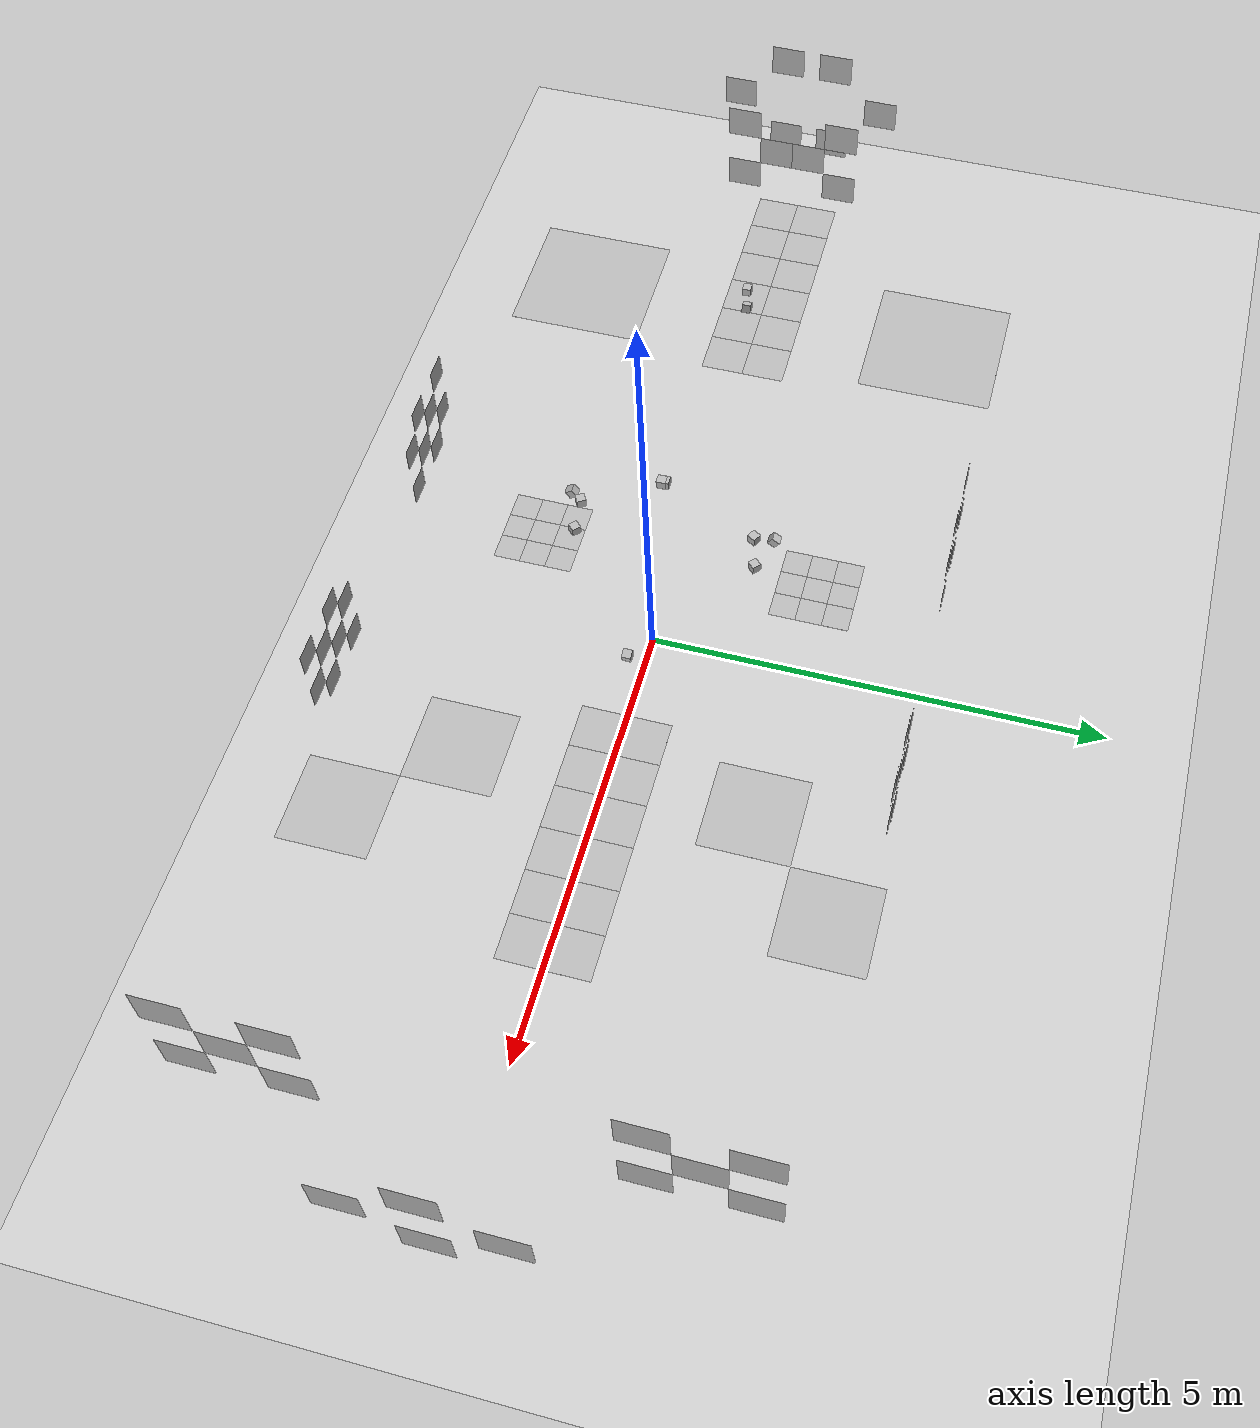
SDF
<sdf version="1.7">
 <world name="default">
  <light name="sun" type="directional">
   <pose>0 0 10 0 -0 0</pose>
   <diffuse>0.8 0.8 0.8 1</diffuse>
   <specular>0.2 0.2 0.2 1</specular>
   <attenuation>
    <range>1000</range>
    <constant>0.9</constant>
    <linear>0.01</linear>
    <quadratic>0.001</quadratic>
   </attenuation>
   <direction>-0.5 0.1 -0.9</direction>
   <spot><inner_angle>0</inner_angle><outer_angle>0</outer_angle><falloff>0</falloff></spot>
  </light>
  <model name="ground_plane">
   <pose>1.6 0 -0.001 0 -0 0</pose>
   <static>1</static>
   <link name="link">
    <collision name="collision">
     <geometry><plane><normal>0 0 1</normal><size>100 100</size></plane></geometry>
     <surface>
      <contact><collide_bitmask>65535</collide_bitmask></contact>
      <friction><ode><mu>100</mu><mu2>50</mu2></ode></friction>
     </surface>
    </collision>
    <visual name="visual">
     <cast_shadows>0</cast_shadows>
     <geometry><plane><normal>0 0 1</normal><size>100 100</size></plane></geometry>
     <material>
      <script><uri>file://media/materials/scripts/gazebo.material</uri><name>Gazebo/Grey</name></script>
     </material>
    </visual>
   </link>
  </model>
  <gravity>0 0 -9.8</gravity>
  <magnetic_field>6e-06 2.3e-05 -4.2e-05</magnetic_field>
  <atmosphere type="adiabatic"/>
  <physics type="ode">
   <max_step_size>0.001</max_step_size>
   <real_time_factor>1</real_time_factor>
   <real_time_update_rate>1000</real_time_update_rate>
  </physics>
  <scene><ambient>0.4 0.4 0.4 1</ambient><background>0.7 0.7 0.7 1</background><shadows>1</shadows></scene>
  <spherical_coordinates>
   <surface_model>EARTH_WGS84</surface_model>
   <latitude_deg>0</latitude_deg>
   <longitude_deg>0</longitude_deg>
   <elevation>0</elevation>
   <heading_deg>0</heading_deg>
  </spherical_coordinates>
  <model name="Apriltag36_10_00107">
   <link name="main">
    <visual name="main_Visual">
     <geometry><box><size>0.5 0.5 0.0001</size></box></geometry>
     <material>
      <script>
       <uri>model://Apriltag36_10_00107/materials/scripts</uri>
       <uri>model://Apriltag36_10_00107/materials/textures</uri>
       <name>Apriltag36_10_00107</name>
      </script>
     </material>
    </visual>
    <collision name="collision"><geometry><box><size>0.5 0.5 0.0001</size></box></geometry></collision>
   </link>
   <static>1</static>
   <pose>3.75 0.25 0 0 -0 0</pose>
  </model>
  <model name="Apriltag36_10_00106">
   <link name="main">
    <visual name="main_Visual">
     <geometry><box><size>0.5 0.5 0.0001</size></box></geometry>
     <material>
      <script>
       <uri>model://Apriltag36_10_00106/materials/scripts</uri>
       <uri>model://Apriltag36_10_00106/materials/textures</uri>
       <name>Apriltag36_10_00106</name>
      </script>
     </material>
    </visual>
    <collision name="collision"><geometry><box><size>0.5 0.5 0.0001</size></box></geometry></collision>
   </link>
   <static>1</static>
   <pose>3.25 0.25 0 0 -0 0</pose>
  </model>
  <model name="Apriltag36_10_00105">
   <link name="main">
    <visual name="main_Visual">
     <geometry><box><size>0.5 0.5 0.0001</size></box></geometry>
     <material>
      <script>
       <uri>model://Apriltag36_10_00105/materials/scripts</uri>
       <uri>model://Apriltag36_10_00105/materials/textures</uri>
       <name>Apriltag36_10_00105</name>
      </script>
     </material>
    </visual>
    <collision name="collision"><geometry><box><size>0.5 0.5 0.0001</size></box></geometry></collision>
   </link>
   <static>1</static>
   <pose>2.75 0.25 0 0 -0 0</pose>
  </model>
  <model name="Apriltag36_10_00104">
   <link name="main">
    <visual name="main_Visual">
     <geometry><box><size>0.5 0.5 0.0001</size></box></geometry>
     <material>
      <script>
       <uri>model://Apriltag36_10_00104/materials/scripts</uri>
       <uri>model://Apriltag36_10_00104/materials/textures</uri>
       <name>Apriltag36_10_00104</name>
      </script>
     </material>
    </visual>
    <collision name="collision"><geometry><box><size>0.5 0.5 0.0001</size></box></geometry></collision>
   </link>
   <static>1</static>
   <pose>2.25 0.25 0 0 -0 0</pose>
  </model>
  <model name="Apriltag36_10_00111">
   <link name="main">
    <visual name="main_Visual">
     <geometry><box><size>0.5 0.5 0.0001</size></box></geometry>
     <material>
      <script>
       <uri>model://Apriltag36_10_00111/materials/scripts</uri>
       <uri>model://Apriltag36_10_00111/materials/textures</uri>
       <name>Apriltag36_10_00111</name>
      </script>
     </material>
    </visual>
    <collision name="collision"><geometry><box><size>0.5 0.5 0.0001</size></box></geometry></collision>
   </link>
   <static>1</static>
   <pose>3.75 -0.25 0 0 -0 0</pose>
  </model>
  <model name="Apriltag36_10_00110">
   <link name="main">
    <visual name="main_Visual">
     <geometry><box><size>0.5 0.5 0.0001</size></box></geometry>
     <material>
      <script>
       <uri>model://Apriltag36_10_00110/materials/scripts</uri>
       <uri>model://Apriltag36_10_00110/materials/textures</uri>
       <name>Apriltag36_10_00110</name>
      </script>
     </material>
    </visual>
    <collision name="collision"><geometry><box><size>0.5 0.5 0.0001</size></box></geometry></collision>
   </link>
   <static>1</static>
   <pose>3.25 -0.25 0 0 -0 0</pose>
  </model>
  <model name="Apriltag36_10_00108">
   <link name="main">
    <visual name="main_Visual">
     <geometry><box><size>0.5 0.5 0.0001</size></box></geometry>
     <material>
      <script>
       <uri>model://Apriltag36_10_00108/materials/scripts</uri>
       <uri>model://Apriltag36_10_00108/materials/textures</uri>
       <name>Apriltag36_10_00108</name>
      </script>
     </material>
    </visual>
    <collision name="collision"><geometry><box><size>0.5 0.5 0.0001</size></box></geometry></collision>
   </link>
   <static>1</static>
   <pose>2.25 -0.25 0 0 -0 0</pose>
  </model>
  <model name="Apriltag36_10_00109">
   <link name="main">
    <visual name="main_Visual">
     <geometry><box><size>0.5 0.5 0.0001</size></box></geometry>
     <material>
      <script>
       <uri>model://Apriltag36_10_00109/materials/scripts</uri>
       <uri>model://Apriltag36_10_00109/materials/textures</uri>
       <name>Apriltag36_10_00109</name>
      </script>
     </material>
    </visual>
    <collision name="collision"><geometry><box><size>0.5 0.5 0.0001</size></box></geometry></collision>
   </link>
   <static>1</static>
   <pose>2.75 -0.25 0 0 -0 0</pose>
  </model>
  <model name="Apriltag36_10_00115">
   <link name="main">
    <visual name="main_Visual">
     <geometry><box><size>0.5 0.5 0.0001</size></box></geometry>
     <material>
      <script>
       <uri>model://Apriltag36_10_00115/materials/scripts</uri>
       <uri>model://Apriltag36_10_00115/materials/textures</uri>
       <name>Apriltag36_10_00115</name>
      </script>
     </material>
    </visual>
    <collision name="collision"><geometry><box><size>0.5 0.5 0.0001</size></box></geometry></collision>
   </link>
   <static>1</static>
   <pose>-5.25 0.25 0 0 -0 0</pose>
  </model>
  <model name="Apriltag36_10_00114">
   <link name="main">
    <visual name="main_Visual">
     <geometry><box><size>0.5 0.5 0.0001</size></box></geometry>
     <material>
      <script>
       <uri>model://Apriltag36_10_00114/materials/scripts</uri>
       <uri>model://Apriltag36_10_00114/materials/textures</uri>
       <name>Apriltag36_10_00114</name>
      </script>
     </material>
    </visual>
    <collision name="collision"><geometry><box><size>0.5 0.5 0.0001</size></box></geometry></collision>
   </link>
   <static>1</static>
   <pose>-5.75 0.25 0 0 -0 0</pose>
  </model>
  <model name="Apriltag36_10_00113">
   <link name="main">
    <visual name="main_Visual">
     <geometry><box><size>0.5 0.5 0.0001</size></box></geometry>
     <material>
      <script>
       <uri>model://Apriltag36_10_00113/materials/scripts</uri>
       <uri>model://Apriltag36_10_00113/materials/textures</uri>
       <name>Apriltag36_10_00113</name>
      </script>
     </material>
    </visual>
    <collision name="collision"><geometry><box><size>0.5 0.5 0.0001</size></box></geometry></collision>
   </link>
   <static>1</static>
   <pose>-6.25 0.25 0 0 -0 0</pose>
  </model>
  <model name="Apriltag36_10_00112">
   <link name="main">
    <visual name="main_Visual">
     <geometry><box><size>0.5 0.5 0.0001</size></box></geometry>
     <material>
      <script>
       <uri>model://Apriltag36_10_00112/materials/scripts</uri>
       <uri>model://Apriltag36_10_00112/materials/textures</uri>
       <name>Apriltag36_10_00112</name>
      </script>
     </material>
    </visual>
    <collision name="collision"><geometry><box><size>0.5 0.5 0.0001</size></box></geometry></collision>
   </link>
   <static>1</static>
   <pose>-6.75 0.25 0 0 -0 0</pose>
  </model>
  <model name="Apriltag36_10_00119">
   <link name="main">
    <visual name="main_Visual">
     <geometry><box><size>0.5 0.5 0.0001</size></box></geometry>
     <material>
      <script>
       <uri>model://Apriltag36_10_00119/materials/scripts</uri>
       <uri>model://Apriltag36_10_00119/materials/textures</uri>
       <name>Apriltag36_10_00119</name>
      </script>
     </material>
    </visual>
    <collision name="collision"><geometry><box><size>0.5 0.5 0.0001</size></box></geometry></collision>
   </link>
   <static>1</static>
   <pose>-5.25 -0.25 0 0 -0 0</pose>
  </model>
  <model name="Apriltag36_10_00118">
   <link name="main">
    <visual name="main_Visual">
     <geometry><box><size>0.5 0.5 0.0001</size></box></geometry>
     <material>
      <script>
       <uri>model://Apriltag36_10_00118/materials/scripts</uri>
       <uri>model://Apriltag36_10_00118/materials/textures</uri>
       <name>Apriltag36_10_00118</name>
      </script>
     </material>
    </visual>
    <collision name="collision"><geometry><box><size>0.5 0.5 0.0001</size></box></geometry></collision>
   </link>
   <static>1</static>
   <pose>-5.75 -0.25 0 0 -0 0</pose>
  </model>
  <model name="Apriltag36_10_00117">
   <link name="main">
    <visual name="main_Visual">
     <geometry><box><size>0.5 0.5 0.0001</size></box></geometry>
     <material>
      <script>
       <uri>model://Apriltag36_10_00117/materials/scripts</uri>
       <uri>model://Apriltag36_10_00117/materials/textures</uri>
       <name>Apriltag36_10_00117</name>
      </script>
     </material>
    </visual>
    <collision name="collision"><geometry><box><size>0.5 0.5 0.0001</size></box></geometry></collision>
   </link>
   <static>1</static>
   <pose>-6.25 -0.25 0 0 -0 0</pose>
  </model>
  <model name="Apriltag36_10_00116">
   <link name="main">
    <visual name="main_Visual">
     <geometry><box><size>0.5 0.5 0.0001</size></box></geometry>
     <material>
      <script>
       <uri>model://Apriltag36_10_00116/materials/scripts</uri>
       <uri>model://Apriltag36_10_00116/materials/textures</uri>
       <name>Apriltag36_10_00116</name>
      </script>
     </material>
    </visual>
    <collision name="collision"><geometry><box><size>0.5 0.5 0.0001</size></box></geometry></collision>
   </link>
   <static>1</static>
   <pose>-6.75 -0.25 0 0 -0 0</pose>
  </model>
  <model name="Apriltag36_11_00410">
   <link name="main">
    <pose>0 0 0 0 -1.5707 0</pose>
    <visual name="main_Visual">
     <geometry><box><size>0.5 0.5 0.0001</size></box></geometry>
     <material>
      <script>
       <uri>model://Apriltag36_11_00410/materials/scripts</uri>
       <uri>model://Apriltag36_11_00410/materials/textures</uri>
       <name>Apriltag36_11_00410</name>
      </script>
     </material>
    </visual>
    <collision name="collision"><geometry><box><size>0.5 0.5 0.0001</size></box></geometry></collision>
   </link>
   <static>1</static>
   <pose>7 0 2 0 -0 0</pose>
  </model>
  <model name="Apriltag36_11_00411">
   <link name="main">
    <pose>0 0 0 0 -1.5707 0</pose>
    <visual name="main_Visual">
     <geometry><box><size>0.5 0.5 0.0001</size></box></geometry>
     <material>
      <script>
       <uri>model://Apriltag36_11_00411/materials/scripts</uri>
       <uri>model://Apriltag36_11_00411/materials/textures</uri>
       <name>Apriltag36_11_00411</name>
      </script>
     </material>
    </visual>
    <collision name="collision"><geometry><box><size>0.5 0.5 0.0001</size></box></geometry></collision>
   </link>
   <static>1</static>
   <pose>7 0.75 1.5 0 -0 0</pose>
  </model>
  <model name="Apriltag36_11_00412">
   <link name="main">
    <pose>0 0 0 0 -1.5707 0</pose>
    <visual name="main_Visual">
     <geometry><box><size>0.5 0.5 0.0001</size></box></geometry>
     <material>
      <script>
       <uri>model://Apriltag36_11_00412/materials/scripts</uri>
       <uri>model://Apriltag36_11_00412/materials/textures</uri>
       <name>Apriltag36_11_00412</name>
      </script>
     </material>
    </visual>
    <collision name="collision"><geometry><box><size>0.5 0.5 0.0001</size></box></geometry></collision>
   </link>
   <static>1</static>
   <pose>7 -0.75 1.5 0 -0 0</pose>
  </model>
  <model name="Apriltag36_11_00413">
   <link name="main">
    <pose>0 0 0 0 -1.5707 0</pose>
    <visual name="main_Visual">
     <geometry><box><size>0.5 0.5 0.0001</size></box></geometry>
     <material>
      <script>
       <uri>model://Apriltag36_11_00413/materials/scripts</uri>
       <uri>model://Apriltag36_11_00413/materials/textures</uri>
       <name>Apriltag36_11_00413</name>
      </script>
     </material>
    </visual>
    <collision name="collision"><geometry><box><size>0.5 0.5 0.0001</size></box></geometry></collision>
   </link>
   <static>1</static>
   <pose>7 0 1 0 -0 0</pose>
  </model>
  <model name="Apriltag36_11_00423">
   <link name="main">
    <pose>0 0 0 3.14159 -1.5707 -0</pose>
    <visual name="main_Visual">
     <geometry><box><size>0.4 0.4 0.0001</size></box></geometry>
     <material>
      <script>
       <uri>model://Apriltag36_11_00423/materials/scripts</uri>
       <uri>model://Apriltag36_11_00423/materials/textures</uri>
       <name>Apriltag36_11_00423</name>
      </script>
     </material>
    </visual>
    <collision name="collision"><geometry><box><size>0.5 0.5 0.0001</size></box></geometry></collision>
   </link>
   <static>1</static>
   <pose>-6.5 0.2 1.3 0 -0 0</pose>
  </model>
  <model name="Apriltag36_11_00422">
   <link name="main">
    <pose>0 0 0 3.14159 -1.5707 -0</pose>
    <visual name="main_Visual">
     <geometry><box><size>0.4 0.4 0.0001</size></box></geometry>
     <material>
      <script>
       <uri>model://Apriltag36_11_00422/materials/scripts</uri>
       <uri>model://Apriltag36_11_00422/materials/textures</uri>
       <name>Apriltag36_11_00422</name>
      </script>
     </material>
    </visual>
    <collision name="collision"><geometry><box><size>0.5 0.5 0.0001</size></box></geometry></collision>
   </link>
   <static>1</static>
   <pose>-6.5 -0.2 1.3 0 -0 0</pose>
  </model>
  <model name="Apriltag36_11_00360">
   <link name="main">
    <pose>0 0 0 0 -1.5707 0</pose>
    <visual name="main_Visual">
     <geometry><box><size>0.5 0.5 0.0001</size></box></geometry>
     <material>
      <script>
       <uri>model://Apriltag36_11_00360/materials/scripts</uri>
       <uri>model://Apriltag36_11_00360/materials/textures</uri>
       <name>Apriltag36_11_00360</name>
      </script>
     </material>
    </visual>
    <collision name="collision"><geometry><box><size>0.5 0.5 0.0001</size></box></geometry></collision>
   </link>
   <static>1</static>
   <pose>6 1.65 2 0 -0 0</pose>
  </model>
  <model name="Apriltag36_11_00362">
   <link name="main">
    <pose>0 0 0 0 -1.5707 0</pose>
    <visual name="main_Visual">
     <geometry><box><size>0.5 0.5 0.0001</size></box></geometry>
     <material>
      <script>
       <uri>model://Apriltag36_11_00362/materials/scripts</uri>
       <uri>model://Apriltag36_11_00362/materials/textures</uri>
       <name>Apriltag36_11_00362</name>
      </script>
     </material>
    </visual>
    <collision name="collision"><geometry><box><size>0.5 0.5 0.0001</size></box></geometry></collision>
   </link>
   <static>1</static>
   <pose>6 1.65 1 0 -0 0</pose>
  </model>
  <model name="Apriltag36_11_00363">
   <link name="main">
    <pose>0 0 0 0 -1.5707 0</pose>
    <visual name="main_Visual">
     <geometry><box><size>0.5 0.5 0.0001</size></box></geometry>
     <material>
      <script>
       <uri>model://Apriltag36_11_00363/materials/scripts</uri>
       <uri>model://Apriltag36_11_00363/materials/textures</uri>
       <name>Apriltag36_11_00363</name>
      </script>
     </material>
    </visual>
    <collision name="collision"><geometry><box><size>0.5 0.5 0.0001</size></box></geometry></collision>
   </link>
   <static>1</static>
   <pose>6 -1.65 2 0 -0 0</pose>
  </model>
  <model name="Apriltag36_11_00365">
   <link name="main">
    <pose>0 0 0 0 -1.5707 0</pose>
    <visual name="main_Visual">
     <geometry><box><size>0.5 0.5 0.0001</size></box></geometry>
     <material>
      <script>
       <uri>model://Apriltag36_11_00365/materials/scripts</uri>
       <uri>model://Apriltag36_11_00365/materials/textures</uri>
       <name>Apriltag36_11_00365</name>
      </script>
     </material>
    </visual>
    <collision name="collision"><geometry><box><size>0.5 0.5 0.0001</size></box></geometry></collision>
   </link>
   <static>1</static>
   <pose>6 -1.65 1 0 -0 0</pose>
  </model>
  <model name="Apriltag36_11_00380">
   <link name="main">
    <pose>0 0 0 1.5707 -1.5707 0</pose>
    <visual name="main_Visual">
     <geometry><box><size>0.3 0.3 0.0001</size></box></geometry>
     <material>
      <script>
       <uri>model://Apriltag36_11_00380/materials/scripts</uri>
       <uri>model://Apriltag36_11_00380/materials/textures</uri>
       <name>Apriltag36_11_00380</name>
      </script>
     </material>
    </visual>
    <collision name="collision"><geometry><box><size>0.5 0.5 0.0001</size></box></geometry></collision>
   </link>
   <static>1</static>
   <pose>1.35 3 1.45 0 -0 0</pose>
  </model>
  <model name="Apriltag36_11_00381">
   <link name="main">
    <pose>0 0 0 1.5707 -1.5707 0</pose>
    <visual name="main_Visual">
     <geometry><box><size>0.3 0.3 0.0001</size></box></geometry>
     <material>
      <script>
       <uri>model://Apriltag36_11_00381/materials/scripts</uri>
       <uri>model://Apriltag36_11_00381/materials/textures</uri>
       <name>Apriltag36_11_00381</name>
      </script>
     </material>
    </visual>
    <collision name="collision"><geometry><box><size>0.5 0.5 0.0001</size></box></geometry></collision>
   </link>
   <static>1</static>
   <pose>1.95 3 1.45 0 -0 0</pose>
  </model>
  <model name="Apriltag36_11_00376">
   <link name="main">
    <pose>0 0 0 1.5707 -1.5707 0</pose>
    <visual name="main_Visual">
     <geometry><box><size>0.3 0.3 0.0001</size></box></geometry>
     <material>
      <script>
       <uri>model://Apriltag36_11_00376/materials/scripts</uri>
       <uri>model://Apriltag36_11_00376/materials/textures</uri>
       <name>Apriltag36_11_00376</name>
      </script>
     </material>
    </visual>
    <collision name="collision"><geometry><box><size>0.5 0.5 0.0001</size></box></geometry></collision>
   </link>
   <static>1</static>
   <pose>1.35 3 0.85 0 -0 0</pose>
  </model>
  <model name="Apriltag36_11_00379">
   <link name="main">
    <pose>0 0 0 1.5707 -1.5707 0</pose>
    <visual name="main_Visual">
     <geometry><box><size>0.3 0.3 0.0001</size></box></geometry>
     <material>
      <script>
       <uri>model://Apriltag36_11_00379/materials/scripts</uri>
       <uri>model://Apriltag36_11_00379/materials/textures</uri>
       <name>Apriltag36_11_00379</name>
      </script>
     </material>
    </visual>
    <collision name="collision"><geometry><box><size>0.5 0.5 0.0001</size></box></geometry></collision>
   </link>
   <static>1</static>
   <pose>1.65 3 1.15 0 -0 0</pose>
  </model>
  <model name="Apriltag36_11_00378">
   <link name="main">
    <pose>0 0 0 1.5707 -1.5707 0</pose>
    <visual name="main_Visual">
     <geometry><box><size>0.3 0.3 0.0001</size></box></geometry>
     <material>
      <script>
       <uri>model://Apriltag36_11_00378/materials/scripts</uri>
       <uri>model://Apriltag36_11_00378/materials/textures</uri>
       <name>Apriltag36_11_00378</name>
      </script>
     </material>
    </visual>
    <collision name="collision"><geometry><box><size>0.5 0.5 0.0001</size></box></geometry></collision>
   </link>
   <static>1</static>
   <pose>1.05 3 1.15 0 -0 0</pose>
  </model>
  <model name="Apriltag36_11_00377">
   <link name="main">
    <pose>0 0 0 1.5707 -1.5707 0</pose>
    <visual name="main_Visual">
     <geometry><box><size>0.3 0.3 0.0001</size></box></geometry>
     <material>
      <script>
       <uri>model://Apriltag36_11_00377/materials/scripts</uri>
       <uri>model://Apriltag36_11_00377/materials/textures</uri>
       <name>Apriltag36_11_00377</name>
      </script>
     </material>
    </visual>
    <collision name="collision"><geometry><box><size>0.5 0.5 0.0001</size></box></geometry></collision>
   </link>
   <static>1</static>
   <pose>1.95 3 0.85 0 -0 0</pose>
  </model>
  <model name="Apriltag36_11_00374">
   <link name="main">
    <pose>0 0 0 1.5707 -1.5707 0</pose>
    <visual name="main_Visual">
     <geometry><box><size>0.3 0.3 0.0001</size></box></geometry>
     <material>
      <script>
       <uri>model://Apriltag36_11_00374/materials/scripts</uri>
       <uri>model://Apriltag36_11_00374/materials/textures</uri>
       <name>Apriltag36_11_00374</name>
      </script>
     </material>
    </visual>
    <collision name="collision"><geometry><box><size>0.5 0.5 0.0001</size></box></geometry></collision>
   </link>
   <static>1</static>
   <pose>1.05 3 0.55 0 -0 0</pose>
  </model>
  <model name="Apriltag36_11_00371">
   <link name="main">
    <pose>0 0 0 1.5707 -1.5707 0</pose>
    <visual name="main_Visual">
     <geometry><box><size>0.3 0.3 0.0001</size></box></geometry>
     <material>
      <script>
       <uri>model://Apriltag36_11_00371/materials/scripts</uri>
       <uri>model://Apriltag36_11_00371/materials/textures</uri>
       <name>Apriltag36_11_00371</name>
      </script>
     </material>
    </visual>
    <collision name="collision"><geometry><box><size>0.5 0.5 0.0001</size></box></geometry></collision>
   </link>
   <static>1</static>
   <pose>-1 3 1.15 0 -0 0</pose>
  </model>
  <model name="Apriltag36_11_00370">
   <link name="main">
    <pose>0 0 0 1.5707 -1.5707 0</pose>
    <visual name="main_Visual">
     <geometry><box><size>0.3 0.3 0.0001</size></box></geometry>
     <material>
      <script>
       <uri>model://Apriltag36_11_00370/materials/scripts</uri>
       <uri>model://Apriltag36_11_00370/materials/textures</uri>
       <name>Apriltag36_11_00370</name>
      </script>
     </material>
    </visual>
    <collision name="collision"><geometry><box><size>0.5 0.5 0.0001</size></box></geometry></collision>
   </link>
   <static>1</static>
   <pose>-1.6 3 1.15 0 -0 0</pose>
  </model>
  <model name="Apriltag36_11_00367">
   <link name="main">
    <pose>0 0 0 1.5707 -1.5707 0</pose>
    <visual name="main_Visual">
     <geometry><box><size>0.3 0.3 0.0001</size></box></geometry>
     <material>
      <script>
       <uri>model://Apriltag36_11_00367/materials/scripts</uri>
       <uri>model://Apriltag36_11_00367/materials/textures</uri>
       <name>Apriltag36_11_00367</name>
      </script>
     </material>
    </visual>
    <collision name="collision"><geometry><box><size>0.5 0.5 0.0001</size></box></geometry></collision>
   </link>
   <static>1</static>
   <pose>-1 3 0.55 0 -0 0</pose>
  </model>
  <model name="Apriltag36_11_00369">
   <link name="main">
    <pose>0 0 0 1.5707 -1.5707 0</pose>
    <visual name="main_Visual">
     <geometry><box><size>0.3 0.3 0.0001</size></box></geometry>
     <material>
      <script>
       <uri>model://Apriltag36_11_00369/materials/scripts</uri>
       <uri>model://Apriltag36_11_00369/materials/textures</uri>
       <name>Apriltag36_11_00369</name>
      </script>
     </material>
    </visual>
    <collision name="collision"><geometry><box><size>0.5 0.5 0.0001</size></box></geometry></collision>
   </link>
   <static>1</static>
   <pose>-1.3 3 0.85 0 -0 0</pose>
  </model>
  <model name="Apriltag36_11_00366">
   <link name="main">
    <pose>0 0 0 1.5707 -1.5707 0</pose>
    <visual name="main_Visual">
     <geometry><box><size>0.3 0.3 0.0001</size></box></geometry>
     <material>
      <script>
       <uri>model://Apriltag36_11_00366/materials/scripts</uri>
       <uri>model://Apriltag36_11_00366/materials/textures</uri>
       <name>Apriltag36_11_00366</name>
      </script>
     </material>
    </visual>
    <collision name="collision"><geometry><box><size>0.5 0.5 0.0001</size></box></geometry></collision>
   </link>
   <static>1</static>
   <pose>-1.6 3 0.55 0 -0 0</pose>
  </model>
  <model name="Apriltag36_11_00386">
   <link name="main">
    <pose>0 0 0 -1.5707 -1.5707 -0</pose>
    <visual name="main_Visual">
     <geometry><box><size>0.3 0.3 0.0001</size></box></geometry>
     <material>
      <script>
       <uri>model://Apriltag36_11_00386/materials/scripts</uri>
       <uri>model://Apriltag36_11_00386/materials/textures</uri>
       <name>Apriltag36_11_00386</name>
      </script>
     </material>
    </visual>
    <collision name="collision"><geometry><box><size>0.5 0.5 0.0001</size></box></geometry></collision>
   </link>
   <static>1</static>
   <pose>1.65 -3 1.15 0 -0 0</pose>
  </model>
  <model name="Apriltag36_11_00385">
   <link name="main">
    <pose>0 0 0 -1.5707 -1.5707 -0</pose>
    <visual name="main_Visual">
     <geometry><box><size>0.3 0.3 0.0001</size></box></geometry>
     <material>
      <script>
       <uri>model://Apriltag36_11_00385/materials/scripts</uri>
       <uri>model://Apriltag36_11_00385/materials/textures</uri>
       <name>Apriltag36_11_00385</name>
      </script>
     </material>
    </visual>
    <collision name="collision"><geometry><box><size>0.5 0.5 0.0001</size></box></geometry></collision>
   </link>
   <static>1</static>
   <pose>1.35 -3 0.85 0 -0 0</pose>
  </model>
  <model name="Apriltag36_11_00389">
   <link name="main">
    <pose>0 0 0 -1.5707 -1.5707 -0</pose>
    <visual name="main_Visual">
     <geometry><box><size>0.3 0.3 0.0001</size></box></geometry>
     <material>
      <script>
       <uri>model://Apriltag36_11_00389/materials/scripts</uri>
       <uri>model://Apriltag36_11_00389/materials/textures</uri>
       <name>Apriltag36_11_00389</name>
      </script>
     </material>
    </visual>
    <collision name="collision"><geometry><box><size>0.5 0.5 0.0001</size></box></geometry></collision>
   </link>
   <static>1</static>
   <pose>1.35 -3 1.45 0 -0 0</pose>
  </model>
  <model name="Apriltag36_11_00387">
   <link name="main">
    <pose>0 0 0 -1.5707 -1.5707 -0</pose>
    <visual name="main_Visual">
     <geometry><box><size>0.3 0.3 0.0001</size></box></geometry>
     <material>
      <script>
       <uri>model://Apriltag36_11_00387/materials/scripts</uri>
       <uri>model://Apriltag36_11_00387/materials/textures</uri>
       <name>Apriltag36_11_00387</name>
      </script>
     </material>
    </visual>
    <collision name="collision"><geometry><box><size>0.5 0.5 0.0001</size></box></geometry></collision>
   </link>
   <static>1</static>
   <pose>1.05 -3 1.15 0 -0 0</pose>
  </model>
  <model name="Apriltag36_11_00382">
   <link name="main">
    <pose>0 0 0 -1.5707 -1.5707 -0</pose>
    <visual name="main_Visual">
     <geometry><box><size>0.3 0.3 0.0001</size></box></geometry>
     <material>
      <script>
       <uri>model://Apriltag36_11_00382/materials/scripts</uri>
       <uri>model://Apriltag36_11_00382/materials/textures</uri>
       <name>Apriltag36_11_00382</name>
      </script>
     </material>
    </visual>
    <collision name="collision"><geometry><box><size>0.5 0.5 0.0001</size></box></geometry></collision>
   </link>
   <static>1</static>
   <pose>1.65 -3 0.55 0 -0 0</pose>
  </model>
  <model name="Apriltag36_11_00383">
   <link name="main">
    <pose>0 0 0 -1.5707 -1.5707 -0</pose>
    <visual name="main_Visual">
     <geometry><box><size>0.3 0.3 0.0001</size></box></geometry>
     <material>
      <script>
       <uri>model://Apriltag36_11_00383/materials/scripts</uri>
       <uri>model://Apriltag36_11_00383/materials/textures</uri>
       <name>Apriltag36_11_00383</name>
      </script>
     </material>
    </visual>
    <collision name="collision"><geometry><box><size>0.5 0.5 0.0001</size></box></geometry></collision>
   </link>
   <static>1</static>
   <pose>1.05 -3 0.55 0 -0 0</pose>
  </model>
  <model name="Apriltag36_11_00396">
   <link name="main">
    <pose>0 0 0 -1.5707 -1.5707 -0</pose>
    <visual name="main_Visual">
     <geometry><box><size>0.3 0.3 0.0001</size></box></geometry>
     <material>
      <script>
       <uri>model://Apriltag36_11_00396/materials/scripts</uri>
       <uri>model://Apriltag36_11_00396/materials/textures</uri>
       <name>Apriltag36_11_00396</name>
      </script>
     </material>
    </visual>
    <collision name="collision"><geometry><box><size>0.5 0.5 0.0001</size></box></geometry></collision>
   </link>
   <static>1</static>
   <pose>-1.3 -3 1.45 0 -0 0</pose>
  </model>
  <model name="Apriltag36_11_00395">
   <link name="main">
    <pose>0 0 0 -1.5707 -1.5707 -0</pose>
    <visual name="main_Visual">
     <geometry><box><size>0.3 0.3 0.0001</size></box></geometry>
     <material>
      <script>
       <uri>model://Apriltag36_11_00395/materials/scripts</uri>
       <uri>model://Apriltag36_11_00395/materials/textures</uri>
       <name>Apriltag36_11_00395</name>
      </script>
     </material>
    </visual>
    <collision name="collision"><geometry><box><size>0.5 0.5 0.0001</size></box></geometry></collision>
   </link>
   <static>1</static>
   <pose>-1.6 -3 1.15 0 -0 0</pose>
  </model>
  <model name="Apriltag36_11_00391">
   <link name="main">
    <pose>0 0 0 -1.5707 -1.5707 -0</pose>
    <visual name="main_Visual">
     <geometry><box><size>0.3 0.3 0.0001</size></box></geometry>
     <material>
      <script>
       <uri>model://Apriltag36_11_00391/materials/scripts</uri>
       <uri>model://Apriltag36_11_00391/materials/textures</uri>
       <name>Apriltag36_11_00391</name>
      </script>
     </material>
    </visual>
    <collision name="collision"><geometry><box><size>0.5 0.5 0.0001</size></box></geometry></collision>
   </link>
   <static>1</static>
   <pose>-1.6 -3 0.55 0 -0 0</pose>
  </model>
  <model name="Apriltag36_11_00397">
   <link name="main">
    <pose>0 0 0 -1.5707 -1.5707 -0</pose>
    <visual name="main_Visual">
     <geometry><box><size>0.3 0.3 0.0001</size></box></geometry>
     <material>
      <script>
       <uri>model://Apriltag36_11_00397/materials/scripts</uri>
       <uri>model://Apriltag36_11_00397/materials/textures</uri>
       <name>Apriltag36_11_00397</name>
      </script>
     </material>
    </visual>
    <collision name="collision"><geometry><box><size>0.5 0.5 0.0001</size></box></geometry></collision>
   </link>
   <static>1</static>
   <pose>-1.9 -3 1.45 0 -0 0</pose>
  </model>
  <model name="Apriltag36_11_00392">
   <link name="main">
    <pose>0 0 0 -1.5707 -1.5707 -0</pose>
    <visual name="main_Visual">
     <geometry><box><size>0.3 0.3 0.0001</size></box></geometry>
     <material>
      <script>
       <uri>model://Apriltag36_11_00392/materials/scripts</uri>
       <uri>model://Apriltag36_11_00392/materials/textures</uri>
       <name>Apriltag36_11_00392</name>
      </script>
     </material>
    </visual>
    <collision name="collision"><geometry><box><size>0.5 0.5 0.0001</size></box></geometry></collision>
   </link>
   <static>1</static>
   <pose>-1.3 -3 0.85 0 -0 0</pose>
  </model>
  <model name="Apriltag36_11_00393">
   <link name="main">
    <pose>0 0 0 -1.5707 -1.5707 -0</pose>
    <visual name="main_Visual">
     <geometry><box><size>0.3 0.3 0.0001</size></box></geometry>
     <material>
      <script>
       <uri>model://Apriltag36_11_00393/materials/scripts</uri>
       <uri>model://Apriltag36_11_00393/materials/textures</uri>
       <name>Apriltag36_11_00393</name>
      </script>
     </material>
    </visual>
    <collision name="collision"><geometry><box><size>0.5 0.5 0.0001</size></box></geometry></collision>
   </link>
   <static>1</static>
   <pose>-1.9 -3 0.85 0 -0 0</pose>
  </model>
  <model name="Apriltag36_10_00124">
   <link name="main">
    <visual name="main_Visual">
     <geometry><box><size>1 1 0.0001</size></box></geometry>
     <material>
      <script>
       <uri>model://Apriltag36_10_00124/materials/scripts</uri>
       <uri>model://Apriltag36_10_00124/materials/textures</uri>
       <name>Apriltag36_10_00124</name>
      </script>
     </material>
    </visual>
    <collision name="collision"><geometry><box><size>1 1 0.0001</size></box></geometry></collision>
   </link>
   <static>1</static>
   <pose>1.8 1.6 0 0 -0 0</pose>
  </model>
  <model name="Apriltag36_10_00125">
   <link name="main">
    <visual name="main_Visual">
     <geometry><box><size>1 1 0.0001</size></box></geometry>
     <material>
      <script>
       <uri>model://Apriltag36_10_00125/materials/scripts</uri>
       <uri>model://Apriltag36_10_00125/materials/textures</uri>
       <name>Apriltag36_10_00125</name>
      </script>
     </material>
    </visual>
    <collision name="collision"><geometry><box><size>1 1 0.0001</size></box></geometry></collision>
   </link>
   <static>1</static>
   <pose>1.8 -1.6 0 0 -0 0</pose>
  </model>
  <model name="Apriltag36_10_00126">
   <link name="main">
    <visual name="main_Visual">
     <geometry><box><size>1.6 1.6 0.0001</size></box></geometry>
     <material>
      <script>
       <uri>model://Apriltag36_10_00126/materials/scripts</uri>
       <uri>model://Apriltag36_10_00126/materials/textures</uri>
       <name>Apriltag36_10_00126</name>
      </script>
     </material>
    </visual>
    <collision name="collision"><geometry><box><size>1.6 1.6 0.0001</size></box></geometry></collision>
   </link>
   <static>1</static>
   <pose>-5 2.2 0 0 -0 0</pose>
  </model>
  <model name="Apriltag36_10_00127">
   <link name="main">
    <visual name="main_Visual">
     <geometry><box><size>1.6 1.6 0.0001</size></box></geometry>
     <material>
      <script>
       <uri>model://Apriltag36_10_00127/materials/scripts</uri>
       <uri>model://Apriltag36_10_00127/materials/textures</uri>
       <name>Apriltag36_10_00127</name>
      </script>
     </material>
    </visual>
    <collision name="collision"><geometry><box><size>1.6 1.6 0.0001</size></box></geometry></collision>
   </link>
   <static>1</static>
   <pose>-5 -2.2 0 0 -0 0</pose>
  </model>
  <model name="Apriltag36_10_00128">
   <link name="main">
    <visual name="main_Visual">
     <geometry><box><size>0.3 0.3 0.0001</size></box></geometry>
     <material>
      <script>
       <uri>model://Apriltag36_10_00128/materials/scripts</uri>
       <uri>model://Apriltag36_10_00128/materials/textures</uri>
       <name>Apriltag36_10_00128</name>
      </script>
     </material>
    </visual>
    <collision name="collision"><geometry><box><size>0.3 0.3 0.0001</size></box></geometry></collision>
   </link>
   <static>1</static>
   <pose>-0.8 1.9 0 0 -0 0</pose>
  </model>
  <model name="Apriltag36_10_00129">
   <link name="main">
    <visual name="main_Visual">
     <geometry><box><size>0.3 0.3 0.0001</size></box></geometry>
     <material>
      <script>
       <uri>model://Apriltag36_10_00129/materials/scripts</uri>
       <uri>model://Apriltag36_10_00129/materials/textures</uri>
       <name>Apriltag36_10_00129</name>
      </script>
     </material>
    </visual>
    <collision name="collision"><geometry><box><size>0.3 0.3 0.0001</size></box></geometry></collision>
   </link>
   <static>1</static>
   <pose>-0.8 1.6 0 0 -0 0</pose>
  </model>
  <model name="Apriltag36_10_00130">
   <link name="main">
    <visual name="main_Visual">
     <geometry><box><size>0.3 0.3 0.0001</size></box></geometry>
     <material>
      <script>
       <uri>model://Apriltag36_10_00130/materials/scripts</uri>
       <uri>model://Apriltag36_10_00130/materials/textures</uri>
       <name>Apriltag36_10_00130</name>
      </script>
     </material>
    </visual>
    <collision name="collision"><geometry><box><size>0.3 0.3 0.0001</size></box></geometry></collision>
   </link>
   <static>1</static>
   <pose>-0.8 1.3 0 0 -0 0</pose>
  </model>
  <model name="Apriltag36_10_00131">
   <link name="main">
    <visual name="main_Visual">
     <geometry><box><size>0.3 0.3 0.0001</size></box></geometry>
     <material>
      <script>
       <uri>model://Apriltag36_10_00131/materials/scripts</uri>
       <uri>model://Apriltag36_10_00131/materials/textures</uri>
       <name>Apriltag36_10_00131</name>
      </script>
     </material>
    </visual>
    <collision name="collision"><geometry><box><size>0.3 0.3 0.0001</size></box></geometry></collision>
   </link>
   <static>1</static>
   <pose>-1.1 1.9 0 0 -0 0</pose>
  </model>
  <model name="Apriltag36_10_00132">
   <link name="main">
    <visual name="main_Visual">
     <geometry><box><size>0.3 0.3 0.0001</size></box></geometry>
     <material>
      <script>
       <uri>model://Apriltag36_10_00132/materials/scripts</uri>
       <uri>model://Apriltag36_10_00132/materials/textures</uri>
       <name>Apriltag36_10_00132</name>
      </script>
     </material>
    </visual>
    <collision name="collision"><geometry><box><size>0.3 0.3 0.0001</size></box></geometry></collision>
   </link>
   <static>1</static>
   <pose>-1.1 1.6 0 0 -0 0</pose>
  </model>
  <model name="Apriltag36_10_00133">
   <link name="main">
    <visual name="main_Visual">
     <geometry><box><size>0.3 0.3 0.0001</size></box></geometry>
     <material>
      <script>
       <uri>model://Apriltag36_10_00133/materials/scripts</uri>
       <uri>model://Apriltag36_10_00133/materials/textures</uri>
       <name>Apriltag36_10_00133</name>
      </script>
     </material>
    </visual>
    <collision name="collision"><geometry><box><size>0.3 0.3 0.0001</size></box></geometry></collision>
   </link>
   <static>1</static>
   <pose>-1.1 1.3 0 0 -0 0</pose>
  </model>
  <model name="Apriltag36_10_00134">
   <link name="main">
    <visual name="main_Visual">
     <geometry><box><size>0.3 0.3 0.0001</size></box></geometry>
     <material>
      <script>
       <uri>model://Apriltag36_10_00134/materials/scripts</uri>
       <uri>model://Apriltag36_10_00134/materials/textures</uri>
       <name>Apriltag36_10_00134</name>
      </script>
     </material>
    </visual>
    <collision name="collision"><geometry><box><size>0.3 0.3 0.0001</size></box></geometry></collision>
   </link>
   <static>1</static>
   <pose>-1.4 1.9 0 0 -0 0</pose>
  </model>
  <model name="Apriltag36_10_00135">
   <link name="main">
    <visual name="main_Visual">
     <geometry><box><size>0.3 0.3 0.0001</size></box></geometry>
     <material>
      <script>
       <uri>model://Apriltag36_10_00135/materials/scripts</uri>
       <uri>model://Apriltag36_10_00135/materials/textures</uri>
       <name>Apriltag36_10_00135</name>
      </script>
     </material>
    </visual>
    <collision name="collision"><geometry><box><size>0.3 0.3 0.0001</size></box></geometry></collision>
   </link>
   <static>1</static>
   <pose>-1.4 1.6 0 0 -0 0</pose>
  </model>
  <model name="Apriltag36_10_00136">
   <link name="main">
    <visual name="main_Visual">
     <geometry><box><size>0.3 0.3 0.0001</size></box></geometry>
     <material>
      <script>
       <uri>model://Apriltag36_10_00136/materials/scripts</uri>
       <uri>model://Apriltag36_10_00136/materials/textures</uri>
       <name>Apriltag36_10_00136</name>
      </script>
     </material>
    </visual>
    <collision name="collision"><geometry><box><size>0.3 0.3 0.0001</size></box></geometry></collision>
   </link>
   <static>1</static>
   <pose>-1.4 1.3 0 0 -0 0</pose>
  </model>
  <model name="Apriltag36_10_00139">
   <link name="main">
    <visual name="main_Visual">
     <geometry><box><size>0.3 0.3 0.0001</size></box></geometry>
     <material>
      <script>
       <uri>model://Apriltag36_10_00139/materials/scripts</uri>
       <uri>model://Apriltag36_10_00139/materials/textures</uri>
       <name>Apriltag36_10_00139</name>
      </script>
     </material>
    </visual>
    <collision name="collision"><geometry><box><size>0.3 0.3 0.0001</size></box></geometry></collision>
   </link>
   <static>1</static>
   <pose>-0.8 -1.9 0 0 -0 0</pose>
  </model>
  <model name="Apriltag36_10_00138">
   <link name="main">
    <visual name="main_Visual">
     <geometry><box><size>0.3 0.3 0.0001</size></box></geometry>
     <material>
      <script>
       <uri>model://Apriltag36_10_00138/materials/scripts</uri>
       <uri>model://Apriltag36_10_00138/materials/textures</uri>
       <name>Apriltag36_10_00138</name>
      </script>
     </material>
    </visual>
    <collision name="collision"><geometry><box><size>0.3 0.3 0.0001</size></box></geometry></collision>
   </link>
   <static>1</static>
   <pose>-0.8 -1.6 0 0 -0 0</pose>
  </model>
  <model name="Apriltag36_10_00137">
   <link name="main">
    <visual name="main_Visual">
     <geometry><box><size>0.3 0.3 0.0001</size></box></geometry>
     <material>
      <script>
       <uri>model://Apriltag36_10_00137/materials/scripts</uri>
       <uri>model://Apriltag36_10_00137/materials/textures</uri>
       <name>Apriltag36_10_00137</name>
      </script>
     </material>
    </visual>
    <collision name="collision"><geometry><box><size>0.3 0.3 0.0001</size></box></geometry></collision>
   </link>
   <static>1</static>
   <pose>-0.8 -1.3 0 0 -0 0</pose>
  </model>
  <model name="Apriltag36_10_00142">
   <link name="main">
    <visual name="main_Visual">
     <geometry><box><size>0.3 0.3 0.0001</size></box></geometry>
     <material>
      <script>
       <uri>model://Apriltag36_10_00142/materials/scripts</uri>
       <uri>model://Apriltag36_10_00142/materials/textures</uri>
       <name>Apriltag36_10_00142</name>
      </script>
     </material>
    </visual>
    <collision name="collision"><geometry><box><size>0.3 0.3 0.0001</size></box></geometry></collision>
   </link>
   <static>1</static>
   <pose>-1.1 -1.9 0 0 -0 0</pose>
  </model>
  <model name="Apriltag36_10_00141">
   <link name="main">
    <visual name="main_Visual">
     <geometry><box><size>0.3 0.3 0.0001</size></box></geometry>
     <material>
      <script>
       <uri>model://Apriltag36_10_00141/materials/scripts</uri>
       <uri>model://Apriltag36_10_00141/materials/textures</uri>
       <name>Apriltag36_10_00141</name>
      </script>
     </material>
    </visual>
    <collision name="collision"><geometry><box><size>0.3 0.3 0.0001</size></box></geometry></collision>
   </link>
   <static>1</static>
   <pose>-1.1 -1.6 0 0 -0 0</pose>
  </model>
  <model name="Apriltag36_10_00140">
   <link name="main">
    <visual name="main_Visual">
     <geometry><box><size>0.3 0.3 0.0001</size></box></geometry>
     <material>
      <script>
       <uri>model://Apriltag36_10_00140/materials/scripts</uri>
       <uri>model://Apriltag36_10_00140/materials/textures</uri>
       <name>Apriltag36_10_00140</name>
      </script>
     </material>
    </visual>
    <collision name="collision"><geometry><box><size>0.3 0.3 0.0001</size></box></geometry></collision>
   </link>
   <static>1</static>
   <pose>-1.1 -1.3 0 0 -0 0</pose>
  </model>
  <model name="Apriltag36_10_00145">
   <link name="main">
    <visual name="main_Visual">
     <geometry><box><size>0.3 0.3 0.0001</size></box></geometry>
     <material>
      <script>
       <uri>model://Apriltag36_10_00145/materials/scripts</uri>
       <uri>model://Apriltag36_10_00145/materials/textures</uri>
       <name>Apriltag36_10_00145</name>
      </script>
     </material>
    </visual>
    <collision name="collision"><geometry><box><size>0.3 0.3 0.0001</size></box></geometry></collision>
   </link>
   <static>1</static>
   <pose>-1.4 -1.9 0 0 -0 0</pose>
  </model>
  <model name="Apriltag36_10_00144">
   <link name="main">
    <visual name="main_Visual">
     <geometry><box><size>0.3 0.3 0.0001</size></box></geometry>
     <material>
      <script>
       <uri>model://Apriltag36_10_00144/materials/scripts</uri>
       <uri>model://Apriltag36_10_00144/materials/textures</uri>
       <name>Apriltag36_10_00144</name>
      </script>
     </material>
    </visual>
    <collision name="collision"><geometry><box><size>0.3 0.3 0.0001</size></box></geometry></collision>
   </link>
   <static>1</static>
   <pose>-1.4 -1.6 0 0 -0 0</pose>
  </model>
  <model name="Apriltag36_10_00143">
   <link name="main">
    <visual name="main_Visual">
     <geometry><box><size>0.3 0.3 0.0001</size></box></geometry>
     <material>
      <script>
       <uri>model://Apriltag36_10_00143/materials/scripts</uri>
       <uri>model://Apriltag36_10_00143/materials/textures</uri>
       <name>Apriltag36_10_00143</name>
      </script>
     </material>
    </visual>
    <collision name="collision"><geometry><box><size>0.3 0.3 0.0001</size></box></geometry></collision>
   </link>
   <static>1</static>
   <pose>-1.4 -1.3 0 0 -0 0</pose>
  </model>
  <model name="front_wide">
   <pose>-0.85793 -0.08982 1.72389 0 -0 0</pose>
   <link name="link">
    <inertial>
     <mass>0.1</mass>
     <inertia>
      <ixx>0.000166667</ixx>
      <iyy>0.000166667</iyy>
      <izz>0.000166667</izz>
      <ixy>0</ixy>
      <ixz>0</ixz>
      <iyz>0</iyz>
     </inertia>
    </inertial>
    <collision name="collision"><geometry><box><size>0.1 0.1 0.1</size></box></geometry></collision>
    <visual name="visual"><geometry><box><size>0.1 0.1 0.1</size></box></geometry></visual>
    <sensor name="camera" type="camera">
     <camera>
      <horizontal_fov>2.094</horizontal_fov>
      <image><width>3840</width><height>2160</height></image>
      <clip><near>0.1</near><far>100</far></clip>
      <distortion>
       <k1>-0.350999</k1>
       <k2>0.19209</k2>
       <k3>-0.0770118</k3>
       <p1>0</p1>
       <p2>0</p2>
       <center>0.49744 0.4991</center>
      </distortion>
      <noise><type>gaussian</type><mean>0</mean><stddev>0.007</stddev></noise>
     </camera>
     <plugin name="camera_controller" filename="libgazebo_ros_camera.so">
      <alwaysOn>1</alwaysOn>
      <updateRate>0.0</updateRate>
      <cameraName>rrbot/camera1</cameraName>
      <imageTopicName>image_raw</imageTopicName>
      <cameraInfoTopicName>camera_info</cameraInfoTopicName>
      <frameName>camera_link</frameName>
      <hackBaseline>0.0</hackBaseline>
      <distortionK1>-0.35099863115140095</distortionK1>
      <distortionK2>0.19209039110108211</distortionK2>
      <distortionK3>-0.07701177238709249</distortionK3>
      <distortionT1>0.0</distortionT1>
      <distortionT2>0.0</distortionT2>
     </plugin>
     <always_on>1</always_on>
     <update_rate>30</update_rate>
     <visualize>1</visualize>
    </sensor>
   </link>
   <static>1</static>
  </model>
  <model name="front_tele">
   <pose>-0.85988 -0.05442 1.72388 0 -0 0</pose>
   <link name="link">
    <inertial>
     <mass>0.1</mass>
     <inertia>
      <ixx>0.000166667</ixx>
      <iyy>0.000166667</iyy>
      <izz>0.000166667</izz>
      <ixy>0</ixy>
      <ixz>0</ixz>
      <iyz>0</iyz>
     </inertia>
    </inertial>
    <collision name="collision"><geometry><box><size>0.1 0.1 0.1</size></box></geometry></collision>
    <visual name="visual"><geometry><box><size>0.1 0.1 0.1</size></box></geometry></visual>
    <sensor name="camera" type="camera">
     <camera>
      <horizontal_fov>0.5235</horizontal_fov>
      <image><width>3840</width><height>2160</height></image>
      <clip><near>0.1</near><far>200</far></clip>
      <distortion><k1>0</k1><k2>0</k2><k3>0</k3><p1>0</p1><p2>0</p2><center>0.49986 0.484568</center></distortion>
      <noise><type>gaussian</type><mean>0</mean><stddev>0.007</stddev></noise>
     </camera>
     <plugin name="camera_controller" filename="libgazebo_ros_camera.so">
      <alwaysOn>1</alwaysOn>
      <updateRate>0.0</updateRate>
      <cameraName>rrbot/front_tele</cameraName>
      <imageTopicName>image_raw</imageTopicName>
      <cameraInfoTopicName>camera_info</cameraInfoTopicName>
      <frameName>camera_link</frameName>
      <hackBaseline>0.0</hackBaseline>
      <focalLength>7319.646289474126</focalLength>
      <distortionK1>0.0</distortionK1>
      <distortionK2>0.0</distortionK2>
      <distortionK3>0.0</distortionK3>
      <distortionT1>0.0</distortionT1>
      <distortionT2>0.0</distortionT2>
     </plugin>
     <always_on>1</always_on>
     <update_rate>30</update_rate>
     <visualize>1</visualize>
    </sensor>
   </link>
   <static>1</static>
  </model>
  <model name="jetour_nrcs_front">
   <pose>0.854392 0 0.970067 0 0.2443 0</pose>
   <link name="link">
    <inertial><mass>0.1</mass></inertial>
    <collision name="collision"><geometry><box><size>0.1 0.1 0.1</size></box></geometry></collision>
    <visual name="visual"><geometry><box><size>0.1 0.1 0.1</size></box></geometry></visual>
    <sensor name="camera" type="wideanglecamera">
     <camera>
      <horizontal_fov>3.40339</horizontal_fov>
      <image><width>1920</width><height>1536</height></image>
      <clip><near>0.1</near><far>100</far></clip>
      <lens>
       <type>stereographic</type>
       <scale_to_hfov>1</scale_to_hfov>
       <cutoff_angle>1.7</cutoff_angle>
       <env_texture_size>512</env_texture_size>
      </lens>
     </camera>
     <always_on>1</always_on>
     <update_rate>30</update_rate>
     <plugin name="camera_controller" filename="libgazebo_ros_camera.so">
      <alwaysOn>1</alwaysOn>
      <updateRate>0.0</updateRate>
      <cameraName>jetour_nrcs_front</cameraName>
      <imageTopicName>jetour_nrcs_front_image_raw</imageTopicName>
      <cameraInfoTopicName>jetour_nrcs_front_camera_info</cameraInfoTopicName>
      <frameName>jetour_nrcs_front_link</frameName>
      <hackBaseline>0.07</hackBaseline>
      <distortionK1>0.0</distortionK1>
      <distortionK2>0.0</distortionK2>
      <distortionK3>0.0</distortionK3>
      <distortionT1>0.0</distortionT1>
      <distortionT2>0.0</distortionT2>
     </plugin>
    </sensor>
   </link>
   <static>1</static>
  </model>
  <model name="jetour_nrcs_right">
   <pose>-0.904 -1.124 1.17333 1e-06 0.6108 -1.5707</pose>
   <link name="link">
    <inertial><mass>0.1</mass></inertial>
    <collision name="collision"><geometry><box><size>0.1 0.1 0.1</size></box></geometry></collision>
    <visual name="visual"><geometry><box><size>0.1 0.1 0.1</size></box></geometry></visual>
    <sensor name="camera" type="wideanglecamera">
     <camera>
      <horizontal_fov>3.40339</horizontal_fov>
      <image><width>1920</width><height>1536</height></image>
      <clip><near>0.1</near><far>100</far></clip>
      <lens>
       <type>stereographic</type>
       <scale_to_hfov>1</scale_to_hfov>
       <cutoff_angle>1.7</cutoff_angle>
       <env_texture_size>512</env_texture_size>
      </lens>
     </camera>
     <always_on>1</always_on>
     <update_rate>30</update_rate>
     <plugin name="camera_controller" filename="libgazebo_ros_camera.so">
      <alwaysOn>1</alwaysOn>
      <updateRate>0.0</updateRate>
      <cameraName>jetour_nrcs_right</cameraName>
      <imageTopicName>jetour_nrcs_right_image_raw</imageTopicName>
      <cameraInfoTopicName>jetour_nrcs_right_camera_info</cameraInfoTopicName>
      <frameName>jetour_nrcs_right_link</frameName>
      <hackBaseline>0.07</hackBaseline>
      <distortionK1>0.0</distortionK1>
      <distortionK2>0.0</distortionK2>
      <distortionK3>0.0</distortionK3>
      <distortionT1>0.0</distortionT1>
      <distortionT2>0.0</distortionT2>
     </plugin>
    </sensor>
   </link>
   <static>1</static>
  </model>
  <model name="jetour_nrcs_rear">
   <pose>-4.22438 0 0.939488 0 0.35303 3.14159</pose>
   <link name="link">
    <inertial><mass>0.1</mass></inertial>
    <collision name="collision"><geometry><box><size>0.1 0.1 0.1</size></box></geometry></collision>
    <visual name="visual"><geometry><box><size>0.1 0.1 0.1</size></box></geometry></visual>
    <sensor name="camera" type="wideanglecamera">
     <camera>
      <horizontal_fov>3.40339</horizontal_fov>
      <image><width>1920</width><height>1536</height></image>
      <clip><near>0.1</near><far>100</far></clip>
      <lens>
       <type>stereographic</type>
       <scale_to_hfov>1</scale_to_hfov>
       <cutoff_angle>1.7</cutoff_angle>
       <env_texture_size>512</env_texture_size>
      </lens>
     </camera>
     <always_on>1</always_on>
     <update_rate>30</update_rate>
     <plugin name="camera_controller" filename="libgazebo_ros_camera.so">
      <alwaysOn>1</alwaysOn>
      <updateRate>0.0</updateRate>
      <cameraName>jetour_nrcs_rear</cameraName>
      <imageTopicName>jetour_nrcs_rear_image_raw</imageTopicName>
      <cameraInfoTopicName>jetour_nrcs_rear_camera_info</cameraInfoTopicName>
      <frameName>jetour_nrcs_rear_link</frameName>
      <hackBaseline>0.07</hackBaseline>
      <distortionK1>0.0</distortionK1>
      <distortionK2>0.0</distortionK2>
      <distortionK3>0.0</distortionK3>
      <distortionT1>0.0</distortionT1>
      <distortionT2>0.0</distortionT2>
     </plugin>
    </sensor>
   </link>
   <static>1</static>
  </model>
  <model name="jetour_nrcs_left">
   <pose>-0.856 1.145 1.11706 1e-06 0.610801 1.5707</pose>
   <link name="link">
    <inertial><mass>0.1</mass></inertial>
    <collision name="collision"><geometry><box><size>0.1 0.1 0.1</size></box></geometry></collision>
    <visual name="visual"><geometry><box><size>0.1 0.1 0.1</size></box></geometry></visual>
    <sensor name="camera" type="wideanglecamera">
     <camera>
      <horizontal_fov>3.40339</horizontal_fov>
      <image><width>1920</width><height>1536</height></image>
      <clip><near>0.1</near><far>100</far></clip>
      <lens>
       <type>stereographic</type>
       <scale_to_hfov>1</scale_to_hfov>
       <cutoff_angle>1.7</cutoff_angle>
       <env_texture_size>512</env_texture_size>
      </lens>
     </camera>
     <always_on>1</always_on>
     <update_rate>30</update_rate>
     <plugin name="camera_controller" filename="libgazebo_ros_camera.so">
      <alwaysOn>1</alwaysOn>
      <updateRate>0.0</updateRate>
      <cameraName>jetour_nrcs_left</cameraName>
      <imageTopicName>jetour_nrcs_left_image_raw</imageTopicName>
      <cameraInfoTopicName>jetour_nrcs_left_camera_info</cameraInfoTopicName>
      <frameName>jetour_nrcs_left_link</frameName>
      <hackBaseline>0.07</hackBaseline>
      <distortionK1>0.0</distortionK1>
      <distortionK2>0.0</distortionK2>
      <distortionK3>0.0</distortionK3>
      <distortionT1>0.0</distortionT1>
      <distortionT2>0.0</distortionT2>
     </plugin>
    </sensor>
   </link>
   <static>1</static>
  </model>
  <model name="Apriltag36_11_00361">
   <link name="main">
    <pose>0 0 0 0 -1.5707 0</pose>
    <visual name="main_Visual">
     <geometry><box><size>0.5 0.5 0.0001</size></box></geometry>
     <material>
      <script>
       <uri>model://Apriltag36_11_00361/materials/scripts</uri>
       <uri>model://Apriltag36_11_00361/materials/textures</uri>
       <name>Apriltag36_11_00361</name>
      </script>
     </material>
    </visual>
    <collision name="collision"><geometry><box><size>0.5 0.5 0.0001</size></box></geometry></collision>
   </link>
   <static>1</static>
   <pose>6 2.15 1.5 0 -0 0</pose>
  </model>
  <model name="Apriltag36_11_00364">
   <link name="main">
    <pose>0 0 0 0 -1.5707 0</pose>
    <visual name="main_Visual">
     <geometry><box><size>0.5 0.5 0.0001</size></box></geometry>
     <material>
      <script>
       <uri>model://Apriltag36_11_00364/materials/scripts</uri>
       <uri>model://Apriltag36_11_00364/materials/textures</uri>
       <name>Apriltag36_11_00364</name>
      </script>
     </material>
    </visual>
    <collision name="collision"><geometry><box><size>0.5 0.5 0.0001</size></box></geometry></collision>
   </link>
   <static>1</static>
   <pose>6 -2.15 1.5 0 -0 0</pose>
  </model>
  <model name="Apriltag36_10_00103">
   <link name="main">
    <visual name="main_Visual">
     <geometry><box><size>0.5 0.5 0.0001</size></box></geometry>
     <material>
      <script>
       <uri>model://Apriltag36_10_00103/materials/scripts</uri>
       <uri>model://Apriltag36_10_00103/materials/textures</uri>
       <name>Apriltag36_10_00103</name>
      </script>
     </material>
    </visual>
    <collision name="collision"><geometry><box><size>0.5 0.5 0.0001</size></box></geometry></collision>
   </link>
   <static>1</static>
   <pose>1.75 -0.25 0 0 -0 0</pose>
  </model>
  <model name="Apriltag36_10_00102">
   <link name="main">
    <visual name="main_Visual">
     <geometry><box><size>0.5 0.5 0.0001</size></box></geometry>
     <material>
      <script>
       <uri>model://Apriltag36_10_00102/materials/scripts</uri>
       <uri>model://Apriltag36_10_00102/materials/textures</uri>
       <name>Apriltag36_10_00102</name>
      </script>
     </material>
    </visual>
    <collision name="collision"><geometry><box><size>0.5 0.5 0.0001</size></box></geometry></collision>
   </link>
   <static>1</static>
   <pose>1.25 -0.25 0 0 -0 0</pose>
  </model>
  <model name="Apriltag36_10_00101">
   <link name="main">
    <visual name="main_Visual">
     <geometry><box><size>0.5 0.5 0.0001</size></box></geometry>
     <material>
      <script>
       <uri>model://Apriltag36_10_00101/materials/scripts</uri>
       <uri>model://Apriltag36_10_00101/materials/textures</uri>
       <name>Apriltag36_10_00101</name>
      </script>
     </material>
    </visual>
    <collision name="collision"><geometry><box><size>0.5 0.5 0.0001</size></box></geometry></collision>
   </link>
   <static>1</static>
   <pose>1.75 0.25 0 0 -0 0</pose>
  </model>
  <model name="Apriltag36_10_00100">
   <link name="main">
    <visual name="main_Visual">
     <geometry><box><size>0.5 0.5 0.0001</size></box></geometry>
     <material>
      <script>
       <uri>model://Apriltag36_10_00100/materials/scripts</uri>
       <uri>model://Apriltag36_10_00100/materials/textures</uri>
       <name>Apriltag36_10_00100</name>
      </script>
     </material>
    </visual>
    <collision name="collision"><geometry><box><size>0.5 0.5 0.0001</size></box></geometry></collision>
   </link>
   <static>1</static>
   <pose>1.25 0.25 0 0 -0 0</pose>
  </model>
  <model name="Apriltag36_10_00122">
   <link name="main">
    <visual name="main_Visual">
     <geometry><box><size>0.5 0.5 0.0001</size></box></geometry>
     <material>
      <script>
       <uri>model://Apriltag36_10_00122/materials/scripts</uri>
       <uri>model://Apriltag36_10_00122/materials/textures</uri>
       <name>Apriltag36_10_00122</name>
      </script>
     </material>
    </visual>
    <collision name="collision"><geometry><box><size>0.5 0.5 0.0001</size></box></geometry></collision>
   </link>
   <static>1</static>
   <pose>-4.75 -0.25 0 0 -0 0</pose>
  </model>
  <model name="Apriltag36_10_00123">
   <link name="main">
    <visual name="main_Visual">
     <geometry><box><size>0.5 0.5 0.0001</size></box></geometry>
     <material>
      <script>
       <uri>model://Apriltag36_10_00123/materials/scripts</uri>
       <uri>model://Apriltag36_10_00123/materials/textures</uri>
       <name>Apriltag36_10_00123</name>
      </script>
     </material>
    </visual>
    <collision name="collision"><geometry><box><size>0.5 0.5 0.0001</size></box></geometry></collision>
   </link>
   <static>1</static>
   <pose>-4.25 -0.25 0 0 -0 0</pose>
  </model>
  <model name="Apriltag36_10_00120">
   <link name="main">
    <visual name="main_Visual">
     <geometry><box><size>0.5 0.5 0.0001</size></box></geometry>
     <material>
      <script>
       <uri>model://Apriltag36_10_00120/materials/scripts</uri>
       <uri>model://Apriltag36_10_00120/materials/textures</uri>
       <name>Apriltag36_10_00120</name>
      </script>
     </material>
    </visual>
    <collision name="collision"><geometry><box><size>0.5 0.5 0.0001</size></box></geometry></collision>
   </link>
   <static>1</static>
   <pose>-4.75 0.25 0 0 -0 0</pose>
  </model>
  <model name="Apriltag36_10_00121">
   <link name="main">
    <visual name="main_Visual">
     <geometry><box><size>0.5 0.5 0.0001</size></box></geometry>
     <material>
      <script>
       <uri>model://Apriltag36_10_00121/materials/scripts</uri>
       <uri>model://Apriltag36_10_00121/materials/textures</uri>
       <name>Apriltag36_10_00121</name>
      </script>
     </material>
    </visual>
    <collision name="collision"><geometry><box><size>0.5 0.5 0.0001</size></box></geometry></collision>
   </link>
   <static>1</static>
   <pose>-4.25 0.25 0 0 -0 0</pose>
  </model>
  <model name="Apriltag36_11_00375">
   <link name="main">
    <pose>0 0 0 1.5707 -1.5707 0</pose>
    <visual name="main_Visual">
     <geometry><box><size>0.3 0.3 0.0001</size></box></geometry>
     <material>
      <script>
       <uri>model://Apriltag36_11_00375/materials/scripts</uri>
       <uri>model://Apriltag36_11_00375/materials/textures</uri>
       <name>Apriltag36_11_00375</name>
      </script>
     </material>
    </visual>
    <collision name="collision"><geometry><box><size>0.5 0.5 0.0001</size></box></geometry></collision>
   </link>
   <static>1</static>
   <pose>1.65 3 0.55 0 -0 0</pose>
  </model>
  <model name="Apriltag36_11_00373">
   <link name="main">
    <pose>0 0 0 1.5707 -1.5707 0</pose>
    <visual name="main_Visual">
     <geometry><box><size>0.3 0.3 0.0001</size></box></geometry>
     <material>
      <script>
       <uri>model://Apriltag36_11_00373/materials/scripts</uri>
       <uri>model://Apriltag36_11_00373/materials/textures</uri>
       <name>Apriltag36_11_00373</name>
      </script>
     </material>
    </visual>
    <collision name="collision"><geometry><box><size>0.5 0.5 0.0001</size></box></geometry></collision>
   </link>
   <static>1</static>
   <pose>-1.3 3 1.45 0 -0 0</pose>
  </model>
  <model name="Apriltag36_11_00372">
   <link name="main">
    <pose>0 0 0 1.5707 -1.5707 0</pose>
    <visual name="main_Visual">
     <geometry><box><size>0.3 0.3 0.0001</size></box></geometry>
     <material>
      <script>
       <uri>model://Apriltag36_11_00372/materials/scripts</uri>
       <uri>model://Apriltag36_11_00372/materials/textures</uri>
       <name>Apriltag36_11_00372</name>
      </script>
     </material>
    </visual>
    <collision name="collision"><geometry><box><size>0.5 0.5 0.0001</size></box></geometry></collision>
   </link>
   <static>1</static>
   <pose>-1.9 3 1.45 0 -0 0</pose>
  </model>
  <model name="Apriltag36_11_00368">
   <link name="main">
    <pose>0 0 0 1.5707 -1.5707 0</pose>
    <visual name="main_Visual">
     <geometry><box><size>0.3 0.3 0.0001</size></box></geometry>
     <material>
      <script>
       <uri>model://Apriltag36_11_00368/materials/scripts</uri>
       <uri>model://Apriltag36_11_00368/materials/textures</uri>
       <name>Apriltag36_11_00368</name>
      </script>
     </material>
    </visual>
    <collision name="collision"><geometry><box><size>0.5 0.5 0.0001</size></box></geometry></collision>
   </link>
   <static>1</static>
   <pose>-1.9 3 0.85 0 -0 0</pose>
  </model>
  <model name="Apriltag36_11_00394">
   <link name="main">
    <pose>0 0 0 -1.5707 -1.5707 -0</pose>
    <visual name="main_Visual">
     <geometry><box><size>0.3 0.3 0.0001</size></box></geometry>
     <material>
      <script>
       <uri>model://Apriltag36_11_00394/materials/scripts</uri>
       <uri>model://Apriltag36_11_00394/materials/textures</uri>
       <name>Apriltag36_11_00394</name>
      </script>
     </material>
    </visual>
    <collision name="collision"><geometry><box><size>0.5 0.5 0.0001</size></box></geometry></collision>
   </link>
   <static>1</static>
   <pose>-1 -3 1.15 0 -0 0</pose>
  </model>
  <model name="Apriltag36_11_00390">
   <link name="main">
    <pose>0 0 0 -1.5707 -1.5707 -0</pose>
    <visual name="main_Visual">
     <geometry><box><size>0.3 0.3 0.0001</size></box></geometry>
     <material>
      <script>
       <uri>model://Apriltag36_11_00390/materials/scripts</uri>
       <uri>model://Apriltag36_11_00390/materials/textures</uri>
       <name>Apriltag36_11_00390</name>
      </script>
     </material>
    </visual>
    <collision name="collision"><geometry><box><size>0.5 0.5 0.0001</size></box></geometry></collision>
   </link>
   <static>1</static>
   <pose>-1 -3 0.55 0 -0 0</pose>
  </model>
  <model name="Apriltag36_11_00388">
   <link name="main">
    <pose>0 0 0 -1.5707 -1.5707 -0</pose>
    <visual name="main_Visual">
     <geometry><box><size>0.3 0.3 0.0001</size></box></geometry>
     <material>
      <script>
       <uri>model://Apriltag36_11_00388/materials/scripts</uri>
       <uri>model://Apriltag36_11_00388/materials/textures</uri>
       <name>Apriltag36_11_00388</name>
      </script>
     </material>
    </visual>
    <collision name="collision"><geometry><box><size>0.5 0.5 0.0001</size></box></geometry></collision>
   </link>
   <static>1</static>
   <pose>1.95 -3 1.45 0 -0 0</pose>
  </model>
  <model name="Apriltag36_11_00384">
   <link name="main">
    <pose>0 0 0 -1.5707 -1.5707 -0</pose>
    <visual name="main_Visual">
     <geometry><box><size>0.3 0.3 0.0001</size></box></geometry>
     <material>
      <script>
       <uri>model://Apriltag36_11_00384/materials/scripts</uri>
       <uri>model://Apriltag36_11_00384/materials/textures</uri>
       <name>Apriltag36_11_00384</name>
      </script>
     </material>
    </visual>
    <collision name="collision"><geometry><box><size>0.5 0.5 0.0001</size></box></geometry></collision>
   </link>
   <static>1</static>
   <pose>1.95 -3 0.85 0 -0 0</pose>
  </model>
  <model name="back_around_cam">
   <pose>-4.22773 0 1.23655 0 0.001378 3.14159</pose>
   <link name="link">
    <inertial>
     <mass>0.1</mass>
     <inertia>
      <ixx>0.000166667</ixx>
      <iyy>0.000166667</iyy>
      <izz>0.000166667</izz>
      <ixy>0</ixy>
      <ixz>0</ixz>
      <iyz>0</iyz>
     </inertia>
    </inertial>
    <collision name="collision"><geometry><box><size>0.1 0.1 0.1</size></box></geometry></collision>
    <visual name="visual"><geometry><box><size>0.1 0.1 0.1</size></box></geometry></visual>
    <sensor name="camera" type="camera">
     <camera>
      <image><width>1920</width><height>1280</height></image>
      <clip><near>0.1</near><far>100</far></clip>
      <distortion>
       <k1>-0.5008</k1>
       <k2>0.2669</k2>
       <k3>-0.1188</k3>
       <p1>0.00016716</p1>
       <p2>-0.00010342</p2>
       <center>0.48462 0.524125</center>
      </distortion>
      <noise><type>gaussian</type><mean>0</mean><stddev>0.007</stddev></noise>
      <horizontal_fov>1.047</horizontal_fov>
     </camera>
     <plugin name="camera_controller" filename="libgazebo_ros_camera.so">
      <alwaysOn>1</alwaysOn>
      <updateRate>0.0</updateRate>
      <cameraName>back_around_cam</cameraName>
      <imageTopicName>back_around_cam_image_raw</imageTopicName>
      <cameraInfoTopicName>back_around_cam_camera_info</cameraInfoTopicName>
      <frameName>camera_link</frameName>
      <hackBaseline>0.0</hackBaseline>
      <Cx>930.47</Cx>
      <Cy>670.88</Cy>
      <focalLength>1967.3</focalLength>
      <distortionK1>-0.5008</distortionK1>
      <distortionK2>>0.2669</distortionK2>
      <distortionK3>-0.1188</distortionK3>
      <distortionT1>0.00016716</distortionT1>
      <distortionT2>-0.00010342</distortionT2>
     </plugin>
     <always_on>1</always_on>
     <update_rate>30</update_rate>
     <visualize>1</visualize>
    </sensor>
   </link>
   <static>1</static>
  </model>
  <model name="around_front_left_cam">
   <pose>-0.707 0.955 1.28 0 -0 1.047</pose>
   <link name="link">
    <inertial>
     <mass>0.1</mass>
     <inertia>
      <ixx>0.000166667</ixx>
      <iyy>0.000166667</iyy>
      <izz>0.000166667</izz>
      <ixy>0</ixy>
      <ixz>0</ixz>
      <iyz>0</iyz>
     </inertia>
    </inertial>
    <collision name="collision"><geometry><box><size>0.1 0.1 0.1</size></box></geometry></collision>
    <visual name="visual"><geometry><box><size>0.1 0.1 0.1</size></box></geometry></visual>
    <sensor name="camera" type="camera">
     <camera>
      <horizontal_fov>1.74533</horizontal_fov>
      <image><width>1920</width><height>1280</height></image>
      <clip><near>0.1</near><far>100</far></clip>
      <distortion>
       <k1>-0.502779</k1>
       <k2>0.329759</k2>
       <k3>-0.30564</k3>
       <p1>0</p1>
       <p2>0</p2>
       <center>0.48477 0.5326</center>
      </distortion>
      <noise><type>gaussian</type><mean>0</mean><stddev>0.007</stddev></noise>
     </camera>
     <plugin name="camera_controller" filename="libgazebo_ros_camera.so">
      <alwaysOn>1</alwaysOn>
      <updateRate>0.0</updateRate>
      <cameraName>qirui_around_front_left_cam</cameraName>
      <imageTopicName>around_front_left_image_raw</imageTopicName>
      <cameraInfoTopicName>around_front_left_camera_info</cameraInfoTopicName>
      <frameName>around_front_left_camera_link</frameName>
      <hackBaseline>0.0</hackBaseline>
      <distortionK1>-0.5027794468124849</distortionK1>
      <distortionK2>0.329759300565976</distortionK2>
      <distortionK3>-0.3056395265387194</distortionK3>
      <distortionT1>0.0</distortionT1>
      <distortionT2>0.0</distortionT2>
     </plugin>
     <always_on>1</always_on>
     <update_rate>30</update_rate>
     <visualize>1</visualize>
    </sensor>
   </link>
   <static>1</static>
  </model>
  <model name="around_front_right_cam">
   <pose>-0.72864 -0.969279 1.28 0 0 -1.047</pose>
   <link name="link">
    <inertial>
     <mass>0.1</mass>
     <inertia>
      <ixx>0.000166667</ixx>
      <iyy>0.000166667</iyy>
      <izz>0.000166667</izz>
      <ixy>0</ixy>
      <ixz>0</ixz>
      <iyz>0</iyz>
     </inertia>
    </inertial>
    <collision name="collision"><geometry><box><size>0.1 0.1 0.1</size></box></geometry></collision>
    <visual name="visual"><geometry><box><size>0.1 0.1 0.1</size></box></geometry></visual>
    <sensor name="camera" type="camera">
     <camera>
      <horizontal_fov>1.74533</horizontal_fov>
      <image><width>1920</width><height>1280</height></image>
      <clip><near>0.1</near><far>100</far></clip>
      <distortion>
       <k1>-0.502779</k1>
       <k2>0.329759</k2>
       <k3>-0.30564</k3>
       <p1>0</p1>
       <p2>0</p2>
       <center>0.48477 0.5326</center>
      </distortion>
      <noise><type>gaussian</type><mean>0</mean><stddev>0.007</stddev></noise>
     </camera>
     <plugin name="camera_controller" filename="libgazebo_ros_camera.so">
      <alwaysOn>1</alwaysOn>
      <updateRate>0.0</updateRate>
      <cameraName>qirui_around_front_right_cam</cameraName>
      <imageTopicName>around_front_right_image_raw</imageTopicName>
      <cameraInfoTopicName>around_front_right_camera_info</cameraInfoTopicName>
      <frameName>around_front_right_camera_link</frameName>
      <hackBaseline>0.0</hackBaseline>
      <distortionK1>0.0</distortionK1>
      <distortionK2>0.0</distortionK2>
      <distortionK3>0.0</distortionK3>
      <distortionT1>0.0</distortionT1>
      <distortionT2>0.0</distortionT2>
     </plugin>
     <always_on>1</always_on>
     <update_rate>30</update_rate>
     <visualize>1</visualize>
    </sensor>
   </link>
   <static>1</static>
  </model>
  <model name="around_rear_left_cam">
   <pose>-0.55438 1.00141 0.99371 0 -0 2.356</pose>
   <link name="link">
    <inertial>
     <mass>0.1</mass>
     <inertia>
      <ixx>0.000166667</ixx>
      <iyy>0.000166667</iyy>
      <izz>0.000166667</izz>
      <ixy>0</ixy>
      <ixz>0</ixz>
      <iyz>0</iyz>
     </inertia>
    </inertial>
    <collision name="collision"><geometry><box><size>0.1 0.1 0.1</size></box></geometry></collision>
    <visual name="visual"><geometry><box><size>0.1 0.1 0.1</size></box></geometry></visual>
    <sensor name="camera" type="camera">
     <camera>
      <horizontal_fov>1.74533</horizontal_fov>
      <image><width>1920</width><height>1280</height></image>
      <clip><near>0.1</near><far>100</far></clip>
      <distortion>
       <k1>-0.502779</k1>
       <k2>0.329759</k2>
       <k3>-0.30564</k3>
       <p1>0</p1>
       <p2>0</p2>
       <center>0.48477 0.5326</center>
      </distortion>
      <noise><type>gaussian</type><mean>0</mean><stddev>0.007</stddev></noise>
     </camera>
     <plugin name="camera_controller" filename="libgazebo_ros_camera.so">
      <alwaysOn>1</alwaysOn>
      <updateRate>0.0</updateRate>
      <cameraName>qirui_around_rear_left_cam</cameraName>
      <imageTopicName>around_rear_left_image_raw</imageTopicName>
      <cameraInfoTopicName>around_rear_left_camera_info</cameraInfoTopicName>
      <frameName>around_rear_left_camera_link</frameName>
      <hackBaseline>0.0</hackBaseline>
      <distortionK1>-0.5027794468124849</distortionK1>
      <distortionK2>0.329759300565976</distortionK2>
      <distortionK3>-0.3056395265387194</distortionK3>
      <distortionT1>0.0</distortionT1>
      <distortionT2>0.0</distortionT2>
     </plugin>
     <always_on>1</always_on>
     <update_rate>30</update_rate>
     <visualize>1</visualize>
    </sensor>
   </link>
   <static>1</static>
  </model>
  <model name="around_rear_right_cam">
   <pose>-0.55438 -1.00141 0.99371 0 0 -2.356</pose>
   <link name="link">
    <inertial>
     <mass>0.1</mass>
     <inertia>
      <ixx>0.000166667</ixx>
      <iyy>0.000166667</iyy>
      <izz>0.000166667</izz>
      <ixy>0</ixy>
      <ixz>0</ixz>
      <iyz>0</iyz>
     </inertia>
    </inertial>
    <collision name="collision"><geometry><box><size>0.1 0.1 0.1</size></box></geometry></collision>
    <visual name="visual"><geometry><box><size>0.1 0.1 0.1</size></box></geometry></visual>
    <sensor name="camera" type="camera">
     <camera>
      <horizontal_fov>1.74533</horizontal_fov>
      <image><width>1920</width><height>1280</height></image>
      <clip><near>0.1</near><far>100</far></clip>
      <distortion>
       <k1>-0.502779</k1>
       <k2>0.329759</k2>
       <k3>-0.30564</k3>
       <p1>0</p1>
       <p2>0</p2>
       <center>0.48477 0.5326</center>
      </distortion>
      <noise><type>gaussian</type><mean>0</mean><stddev>0.007</stddev></noise>
     </camera>
     <plugin name="camera_controller" filename="libgazebo_ros_camera.so">
      <alwaysOn>1</alwaysOn>
      <updateRate>0.0</updateRate>
      <cameraName>qirui_around_rear_right_cam</cameraName>
      <imageTopicName>around_rear_right_image_raw</imageTopicName>
      <cameraInfoTopicName>around_rear_right_camera_info</cameraInfoTopicName>
      <frameName>around_rear_right_camera_link</frameName>
      <hackBaseline>0.0</hackBaseline>
      <distortionK1>-0.5027794468124849</distortionK1>
      <distortionK2>>0.329759300565976</distortionK2>
      <distortionK3>-0.3056395265387194</distortionK3>
      <distortionT1>0.0</distortionT1>
      <distortionT2>0.0</distortionT2>
     </plugin>
     <always_on>1</always_on>
     <update_rate>30</update_rate>
     <visualize>1</visualize>
    </sensor>
   </link>
   <static>1</static>
  </model>
  <model name="Apriltag36_11_00400">
   <link name="main">
    <pose>0 0 0 0 -1.5707 0</pose>
    <visual name="main_Visual">
     <geometry><box><size>0.5 0.5 0.0001</size></box></geometry>
     <material>
      <script>
       <uri>model://Apriltag36_11_00400/materials/scripts</uri>
       <uri>model://Apriltag36_11_00400/materials/textures</uri>
       <name>Apriltag36_11_00400</name>
      </script>
     </material>
    </visual>
    <collision name="collision"><geometry><box><size>0.5 0.5 0.0001</size></box></geometry></collision>
   </link>
   <static>1</static>
   <pose>6 2.65 2 0 -0 0</pose>
  </model>
  <model name="Apriltag36_11_00401">
   <link name="main">
    <pose>0 0 0 0 -1.5707 0</pose>
    <visual name="main_Visual">
     <geometry><box><size>0.5 0.5 0.0001</size></box></geometry>
     <material>
      <script>
       <uri>model://Apriltag36_11_00401/materials/scripts</uri>
       <uri>model://Apriltag36_11_00401/materials/textures</uri>
       <name>Apriltag36_11_00401</name>
      </script>
     </material>
    </visual>
    <collision name="collision"><geometry><box><size>0.5 0.5 0.0001</size></box></geometry></collision>
   </link>
   <static>1</static>
   <pose>6 2.65 1 0 -0 0</pose>
  </model>
  <model name="Apriltag36_11_00402">
   <link name="main">
    <pose>0 0 0 0 -1.5707 0</pose>
    <visual name="main_Visual">
     <geometry><box><size>0.5 0.5 0.0001</size></box></geometry>
     <material>
      <script>
       <uri>model://Apriltag36_11_00402/materials/scripts</uri>
       <uri>model://Apriltag36_11_00402/materials/textures</uri>
       <name>Apriltag36_11_00402</name>
      </script>
     </material>
    </visual>
    <collision name="collision"><geometry><box><size>0.5 0.5 0.0001</size></box></geometry></collision>
   </link>
   <static>1</static>
   <pose>6 -2.65 2 0 -0 0</pose>
  </model>
  <model name="Apriltag36_11_00403">
   <link name="main">
    <pose>0 0 0 0 -1.5707 0</pose>
    <visual name="main_Visual">
     <geometry><box><size>0.5 0.5 0.0001</size></box></geometry>
     <material>
      <script>
       <uri>model://Apriltag36_11_00403/materials/scripts</uri>
       <uri>model://Apriltag36_11_00403/materials/textures</uri>
       <name>Apriltag36_11_00403</name>
      </script>
     </material>
    </visual>
    <collision name="collision"><geometry><box><size>0.5 0.5 0.0001</size></box></geometry></collision>
   </link>
   <static>1</static>
   <pose>6 -2.65 1 0 -0 0</pose>
  </model>
  <model name="Apriltag36_10_00150">
   <link name="main">
    <visual name="main_Visual">
     <geometry><box><size>1 1 0.0001</size></box></geometry>
     <material>
      <script>
       <uri>model://Apriltag36_10_00150/materials/scripts</uri>
       <uri>model://Apriltag36_10_00150/materials/textures</uri>
       <name>Apriltag36_10_00150</name>
      </script>
     </material>
    </visual>
    <collision name="collision"><geometry><box><size>1 1 0.0001</size></box></geometry></collision>
   </link>
   <static>1</static>
   <pose>2.8 2.6 0 0 -0 0</pose>
  </model>
  <model name="Apriltag36_10_00151">
   <link name="main">
    <visual name="main_Visual">
     <geometry><box><size>1 1 0.0001</size></box></geometry>
     <material>
      <script>
       <uri>model://Apriltag36_10_00151/materials/scripts</uri>
       <uri>model://Apriltag36_10_00151/materials/textures</uri>
       <name>Apriltag36_10_00151</name>
      </script>
     </material>
    </visual>
    <collision name="collision"><geometry><box><size>1 1 0.0001</size></box></geometry></collision>
   </link>
   <static>1</static>
   <pose>2.8 -2.6 0 0 -0 0</pose>
  </model>
  <model name="Apriltag36_11_00420">
   <link name="main">
    <pose>0 0 0 3.14159 -1.5707 -0</pose>
    <visual name="main_Visual">
     <geometry><box><size>0.4 0.4 0.0001</size></box></geometry>
     <material>
      <script>
       <uri>model://Apriltag36_11_00420/materials/scripts</uri>
       <uri>model://Apriltag36_11_00420/materials/textures</uri>
       <name>Apriltag36_11_00420</name>
      </script>
     </material>
    </visual>
    <collision name="collision"><geometry><box><size>0.5 0.5 0.0001</size></box></geometry></collision>
   </link>
   <static>1</static>
   <pose>-6.5 -0.6 1.7 0 -0 0</pose>
  </model>
  <model name="Apriltag36_11_00424">
   <link name="main">
    <pose>0 0 0 3.14159 -1.5707 -0</pose>
    <visual name="main_Visual">
     <geometry><box><size>0.4 0.4 0.0001</size></box></geometry>
     <material>
      <script>
       <uri>model://Apriltag36_11_00424/materials/scripts</uri>
       <uri>model://Apriltag36_11_00424/materials/textures</uri>
       <name>Apriltag36_11_00424</name>
      </script>
     </material>
    </visual>
    <collision name="collision"><geometry><box><size>0.5 0.5 0.0001</size></box></geometry></collision>
   </link>
   <static>1</static>
   <pose>-6.5 -0.6 0.9 0 -0 0</pose>
  </model>
  <model name="Apriltag36_11_00421">
   <link name="main">
    <pose>0 0 0 3.14159 -1.5707 -0</pose>
    <visual name="main_Visual">
     <geometry><box><size>0.4 0.4 0.0001</size></box></geometry>
     <material>
      <script>
       <uri>model://Apriltag36_11_00421/materials/scripts</uri>
       <uri>model://Apriltag36_11_00421/materials/textures</uri>
       <name>Apriltag36_11_00421</name>
      </script>
     </material>
    </visual>
    <collision name="collision"><geometry><box><size>0.5 0.5 0.0001</size></box></geometry></collision>
   </link>
   <static>1</static>
   <pose>-6.5 0.6 1.7 0 -0 0</pose>
  </model>
  <model name="Apriltag36_11_00425">
   <link name="main">
    <pose>0 0 0 3.14159 -1.5707 -0</pose>
    <visual name="main_Visual">
     <geometry><box><size>0.4 0.4 0.0001</size></box></geometry>
     <material>
      <script>
       <uri>model://Apriltag36_11_00425/materials/scripts</uri>
       <uri>model://Apriltag36_11_00425/materials/textures</uri>
       <name>Apriltag36_11_00425</name>
      </script>
     </material>
    </visual>
    <collision name="collision"><geometry><box><size>0.5 0.5 0.0001</size></box></geometry></collision>
   </link>
   <static>1</static>
   <pose>-6.5 0.6 0.9 0 -0 0</pose>
  </model>
  <model name="Apriltag36_11_00430">
   <link name="main">
    <pose>0 0 0 3.14159 -1.5707 -0</pose>
    <visual name="main_Visual">
     <geometry><box><size>0.4 0.4 0.0001</size></box></geometry>
     <material>
      <script>
       <uri>model://Apriltag36_11_00430/materials/scripts</uri>
       <uri>model://Apriltag36_11_00430/materials/textures</uri>
       <name>Apriltag36_11_00430</name>
      </script>
     </material>
    </visual>
    <collision name="collision"><geometry><box><size>0.5 0.5 0.0001</size></box></geometry></collision>
   </link>
   <static>1</static>
   <pose>-7.5 -0.3 1.9 0 -0 0</pose>
  </model>
  <model name="Apriltag36_11_00431">
   <link name="main">
    <pose>0 0 0 3.14159 -1.5707 -0</pose>
    <visual name="main_Visual">
     <geometry><box><size>0.4 0.4 0.0001</size></box></geometry>
     <material>
      <script>
       <uri>model://Apriltag36_11_00431/materials/scripts</uri>
       <uri>model://Apriltag36_11_00431/materials/textures</uri>
       <name>Apriltag36_11_00431</name>
      </script>
     </material>
    </visual>
    <collision name="collision"><geometry><box><size>0.5 0.5 0.0001</size></box></geometry></collision>
   </link>
   <static>1</static>
   <pose>-7.5 0.3 1.9 0 -0 0</pose>
  </model>
  <model name="Apriltag36_11_00434">
   <link name="main">
    <pose>0 0 0 3.14159 -1.5707 -0</pose>
    <visual name="main_Visual">
     <geometry><box><size>0.4 0.4 0.0001</size></box></geometry>
     <material>
      <script>
       <uri>model://Apriltag36_11_00434/materials/scripts</uri>
       <uri>model://Apriltag36_11_00434/materials/textures</uri>
       <name>Apriltag36_11_00434</name>
      </script>
     </material>
    </visual>
    <collision name="collision"><geometry><box><size>0.5 0.5 0.0001</size></box></geometry></collision>
   </link>
   <static>1</static>
   <pose>-7.5 -0.3 0.7 0 -0 0</pose>
  </model>
  <model name="Apriltag36_11_00435">
   <link name="main">
    <pose>0 0 0 3.14159 -1.5707 -0</pose>
    <visual name="main_Visual">
     <geometry><box><size>0.4 0.4 0.0001</size></box></geometry>
     <material>
      <script>
       <uri>model://Apriltag36_11_00435/materials/scripts</uri>
       <uri>model://Apriltag36_11_00435/materials/textures</uri>
       <name>Apriltag36_11_00435</name>
      </script>
     </material>
    </visual>
    <collision name="collision"><geometry><box><size>0.5 0.5 0.0001</size></box></geometry></collision>
   </link>
   <static>1</static>
   <pose>-7.5 0.3 0.7 0 -0 0</pose>
  </model>
  <model name="Apriltag36_11_00432">
   <link name="main">
    <pose>0 0 0 3.14159 -1.5707 -0</pose>
    <visual name="main_Visual">
     <geometry><box><size>0.4 0.4 0.0001</size></box></geometry>
     <material>
      <script>
       <uri>model://Apriltag36_11_00432/materials/scripts</uri>
       <uri>model://Apriltag36_11_00432/materials/textures</uri>
       <name>Apriltag36_11_00432</name>
      </script>
     </material>
    </visual>
    <collision name="collision"><geometry><box><size>0.5 0.5 0.0001</size></box></geometry></collision>
   </link>
   <static>1</static>
   <pose>-7.5 -0.9 1.3 0 -0 0</pose>
  </model>
  <model name="Apriltag36_11_00433">
   <link name="main">
    <pose>0 0 0 3.14159 -1.5707 -0</pose>
    <visual name="main_Visual">
     <geometry><box><size>0.4 0.4 0.0001</size></box></geometry>
     <material>
      <script>
       <uri>model://Apriltag36_11_00433/materials/scripts</uri>
       <uri>model://Apriltag36_11_00433/materials/textures</uri>
       <name>Apriltag36_11_00433</name>
      </script>
     </material>
    </visual>
    <collision name="collision"><geometry><box><size>0.5 0.5 0.0001</size></box></geometry></collision>
   </link>
   <static>1</static>
   <pose>-7.5 0.9 1.3 0 -0 0</pose>
  </model>
 </world>
</sdf>
